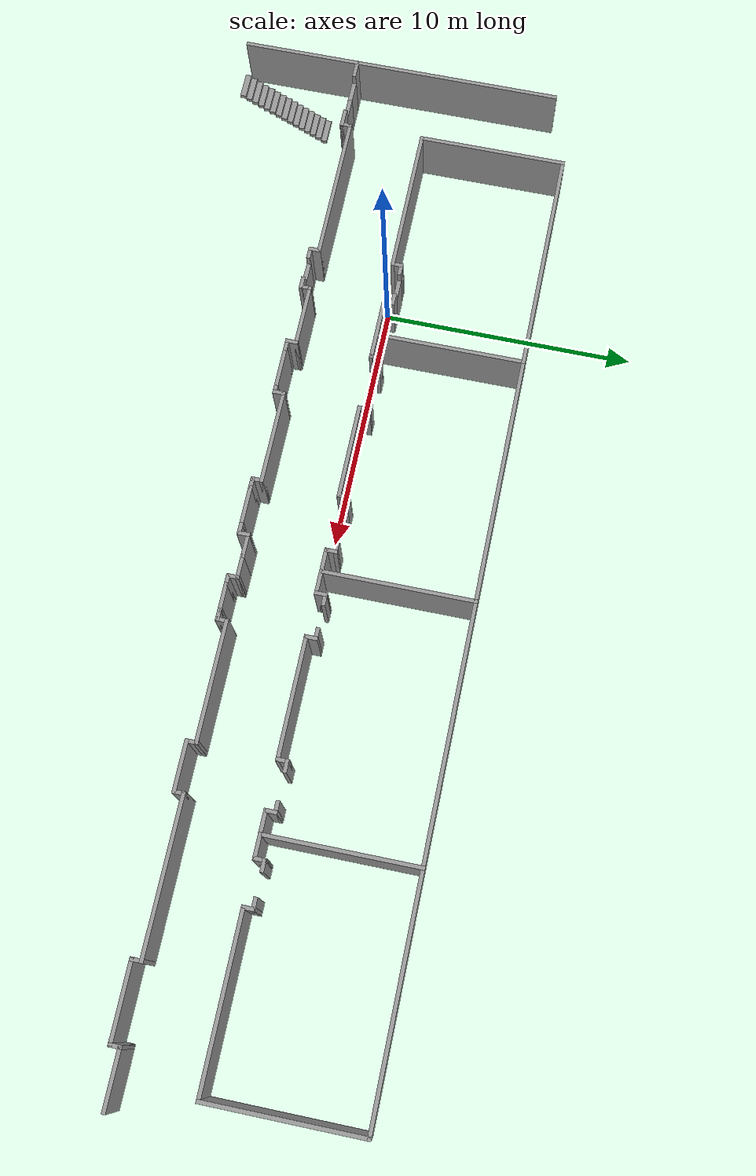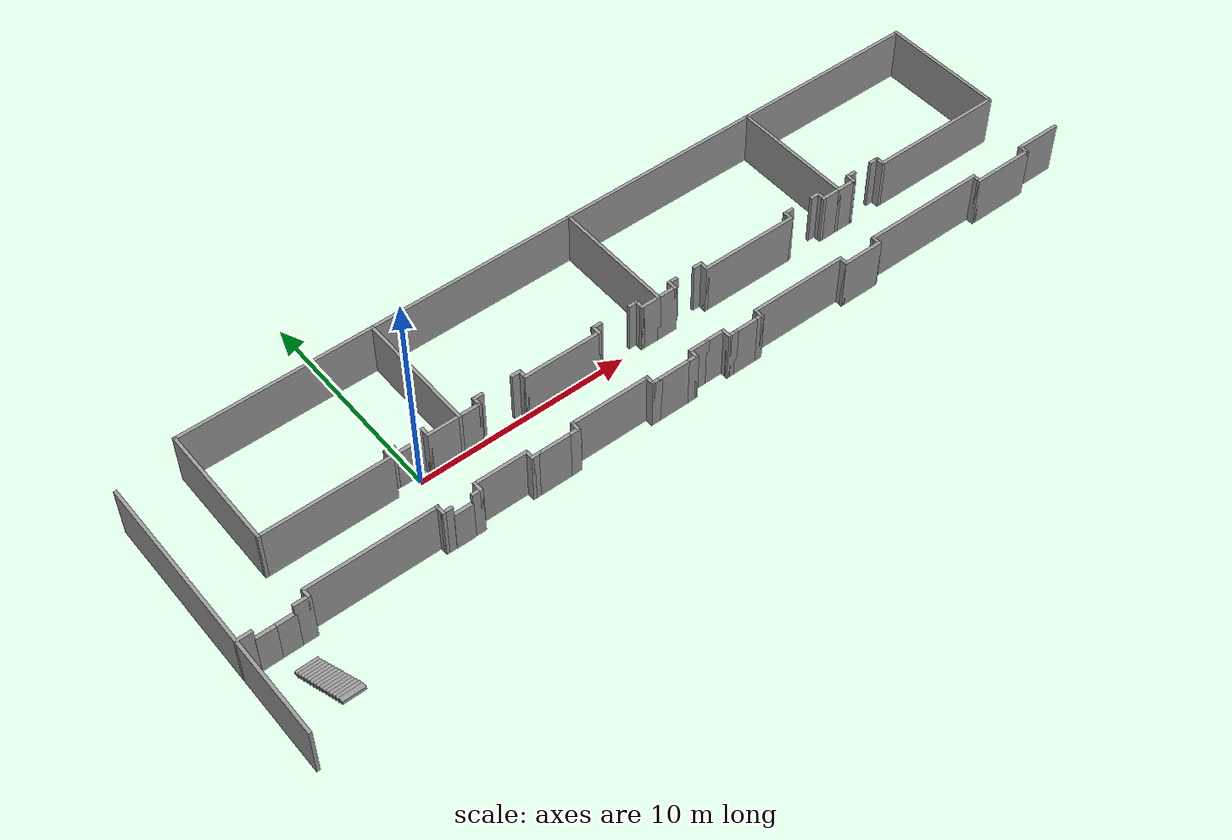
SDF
<?xml version='1.0'?>
<sdf version='1.6'>
  <model name='corridor'>
    <pose frame=''>10.825 -1.075 0 0 -0 0</pose>
    <link name='Door_1'>
      <collision name='Door_1_Collision'>
        <geometry>
          <box>
            <size>0.9 0.17 2</size>
          </box>
        </geometry>
        <pose frame=''>0 0 1 0 -0 0</pose>
      </collision>
      <visual name='Door_1_Visual'>
        <pose frame=''>0 0 1 0 -0 0</pose>
        <geometry>
          <box>
            <size>0.9 0.17 2</size>
          </box>
        </geometry>
        <material>
          <script>
            <uri>file://media/materials/scripts/gazebo.material</uri>
            <name>Gazebo/Grey</name>
          </script>
        </material>
      </visual>
      <pose frame=''>-18.8694 -2.273 0 0 -0 0</pose>
    </link>
    <link name='Door_4'>
      <collision name='Door_4_Collision'>
        <geometry>
          <box>
            <size>0.9 0.17 2</size>
          </box>
        </geometry>
        <pose frame=''>0 0 1 0 -0 0</pose>
      </collision>
      <visual name='Door_4_Visual'>
        <pose frame=''>0 0 1 0 -0 0</pose>
        <geometry>
          <box>
            <size>0.9 0.17 2</size>
          </box>
        </geometry>
        <material>
          <script>
            <uri>file://media/materials/scripts/gazebo.material</uri>
            <name>Gazebo/Grey</name>
          </script>
        </material>
      </visual>
      <pose frame=''>-11.125 1.425 0 0 -0 3.14042</pose>
    </link>
    <link name='Door_6'>
      <collision name='Door_6_Collision'>
        <geometry>
          <box>
            <size>0.9 0.17 2</size>
          </box>
        </geometry>
        <pose frame=''>0 0 1 0 -0 0</pose>
      </collision>
      <visual name='Door_6_Visual'>
        <pose frame=''>0 0 1 0 -0 0</pose>
        <geometry>
          <box>
            <size>0.9 0.17 2</size>
          </box>
        </geometry>
        <material>
          <script>
            <uri>file://media/materials/scripts/gazebo.material</uri>
            <name>Gazebo/Grey</name>
          </script>
        </material>
      </visual>
      <pose frame=''>-19.7205 -2.27816 0 0 -0 0</pose>
    </link>
    <link name='Door_7'>
      <collision name='Door_7_Collision'>
        <geometry>
          <box>
            <size>0.9 0.17 2</size>
          </box>
        </geometry>
        <pose frame=''>0 0 1 0 -0 0</pose>
      </collision>
      <visual name='Door_7_Visual'>
        <pose frame=''>0 0 1 0 -0 0</pose>
        <geometry>
          <box>
            <size>0.9 0.17 2</size>
          </box>
        </geometry>
        <material>
          <script>
            <uri>file://media/materials/scripts/gazebo.material</uri>
            <name>Gazebo/Grey</name>
          </script>
        </material>
      </visual>
      <pose frame=''>-11.125 -2.279 0 0 -0 0</pose>
    </link>
    <link name='Stairs_1'>
      <visual name='Stairs_1_Visual_0'>
        <pose frame=''>-18.825 -3.29167 0.083333 0 -0 0</pose>
        <geometry>
          <box>
            <size>1 0.233333 0.166667</size>
          </box>
        </geometry>
        <material>
          <script>
            <uri>file://media/materials/scripts/gazebo.material</uri>
            <name>Gazebo/Grey</name>
          </script>
          <ambient>1 1 1 1</ambient>
        </material>
        <meta>
          <layer>0</layer>
        </meta>
      </visual>
      <collision name='Stairs_1_Collision_0'>
        <geometry>
          <box>
            <size>1 0.233333 0.166667</size>
          </box>
        </geometry>
        <pose frame=''>-18.825 -3.29167 0.083333 0 -0 0</pose>
      </collision>
      <visual name='Stairs_1_Visual_1'>
        <pose frame=''>-18.825 -3.525 0.25 0 -0 0</pose>
        <geometry>
          <box>
            <size>1 0.233333 0.166667</size>
          </box>
        </geometry>
        <material>
          <script>
            <uri>file://media/materials/scripts/gazebo.material</uri>
            <name>Gazebo/Grey</name>
          </script>
          <ambient>1 1 1 1</ambient>
        </material>
        <meta>
          <layer>0</layer>
        </meta>
      </visual>
      <collision name='Stairs_1_Collision_1'>
        <geometry>
          <box>
            <size>1 0.233333 0.166667</size>
          </box>
        </geometry>
        <pose frame=''>-18.825 -3.525 0.25 0 -0 0</pose>
      </collision>
      <visual name='Stairs_1_Visual_2'>
        <pose frame=''>-18.825 -3.75833 0.416667 0 -0 0</pose>
        <geometry>
          <box>
            <size>1 0.233333 0.166667</size>
          </box>
        </geometry>
        <material>
          <script>
            <uri>file://media/materials/scripts/gazebo.material</uri>
            <name>Gazebo/Grey</name>
          </script>
          <ambient>1 1 1 1</ambient>
        </material>
        <meta>
          <layer>0</layer>
        </meta>
      </visual>
      <collision name='Stairs_1_Collision_2'>
        <geometry>
          <box>
            <size>1 0.233333 0.166667</size>
          </box>
        </geometry>
        <pose frame=''>-18.825 -3.75833 0.416667 0 -0 0</pose>
      </collision>
      <visual name='Stairs_1_Visual_3'>
        <pose frame=''>-18.825 -3.99167 0.583333 0 -0 0</pose>
        <geometry>
          <box>
            <size>1 0.233333 0.166667</size>
          </box>
        </geometry>
        <material>
          <script>
            <uri>file://media/materials/scripts/gazebo.material</uri>
            <name>Gazebo/Grey</name>
          </script>
          <ambient>1 1 1 1</ambient>
        </material>
        <meta>
          <layer>0</layer>
        </meta>
      </visual>
      <collision name='Stairs_1_Collision_3'>
        <geometry>
          <box>
            <size>1 0.233333 0.166667</size>
          </box>
        </geometry>
        <pose frame=''>-18.825 -3.99167 0.583333 0 -0 0</pose>
      </collision>
      <visual name='Stairs_1_Visual_4'>
        <pose frame=''>-18.825 -4.225 0.75 0 -0 0</pose>
        <geometry>
          <box>
            <size>1 0.233333 0.166667</size>
          </box>
        </geometry>
        <material>
          <script>
            <uri>file://media/materials/scripts/gazebo.material</uri>
            <name>Gazebo/Grey</name>
          </script>
          <ambient>1 1 1 1</ambient>
        </material>
        <meta>
          <layer>0</layer>
        </meta>
      </visual>
      <collision name='Stairs_1_Collision_4'>
        <geometry>
          <box>
            <size>1 0.233333 0.166667</size>
          </box>
        </geometry>
        <pose frame=''>-18.825 -4.225 0.75 0 -0 0</pose>
      </collision>
      <visual name='Stairs_1_Visual_5'>
        <pose frame=''>-18.825 -4.45833 0.916667 0 -0 0</pose>
        <geometry>
          <box>
            <size>1 0.233333 0.166667</size>
          </box>
        </geometry>
        <material>
          <script>
            <uri>file://media/materials/scripts/gazebo.material</uri>
            <name>Gazebo/Grey</name>
          </script>
          <ambient>1 1 1 1</ambient>
        </material>
        <meta>
          <layer>0</layer>
        </meta>
      </visual>
      <collision name='Stairs_1_Collision_5'>
        <geometry>
          <box>
            <size>1 0.233333 0.166667</size>
          </box>
        </geometry>
        <pose frame=''>-18.825 -4.45833 0.916667 0 -0 0</pose>
      </collision>
      <visual name='Stairs_1_Visual_6'>
        <pose frame=''>-18.825 -4.69167 1.08333 0 -0 0</pose>
        <geometry>
          <box>
            <size>1 0.233333 0.166667</size>
          </box>
        </geometry>
        <material>
          <script>
            <uri>file://media/materials/scripts/gazebo.material</uri>
            <name>Gazebo/Grey</name>
          </script>
          <ambient>1 1 1 1</ambient>
        </material>
        <meta>
          <layer>0</layer>
        </meta>
      </visual>
      <collision name='Stairs_1_Collision_6'>
        <geometry>
          <box>
            <size>1 0.233333 0.166667</size>
          </box>
        </geometry>
        <pose frame=''>-18.825 -4.69167 1.08333 0 -0 0</pose>
      </collision>
      <visual name='Stairs_1_Visual_7'>
        <pose frame=''>-18.825 -4.925 1.25 0 -0 0</pose>
        <geometry>
          <box>
            <size>1 0.233333 0.166667</size>
          </box>
        </geometry>
        <material>
          <script>
            <uri>file://media/materials/scripts/gazebo.material</uri>
            <name>Gazebo/Grey</name>
          </script>
          <ambient>1 1 1 1</ambient>
        </material>
        <meta>
          <layer>0</layer>
        </meta>
      </visual>
      <collision name='Stairs_1_Collision_7'>
        <geometry>
          <box>
            <size>1 0.233333 0.166667</size>
          </box>
        </geometry>
        <pose frame=''>-18.825 -4.925 1.25 0 -0 0</pose>
      </collision>
      <visual name='Stairs_1_Visual_8'>
        <pose frame=''>-18.825 -5.15833 1.41667 0 -0 0</pose>
        <geometry>
          <box>
            <size>1 0.233333 0.166667</size>
          </box>
        </geometry>
        <material>
          <script>
            <uri>file://media/materials/scripts/gazebo.material</uri>
            <name>Gazebo/Grey</name>
          </script>
          <ambient>1 1 1 1</ambient>
        </material>
        <meta>
          <layer>0</layer>
        </meta>
      </visual>
      <collision name='Stairs_1_Collision_8'>
        <geometry>
          <box>
            <size>1 0.233333 0.166667</size>
          </box>
        </geometry>
        <pose frame=''>-18.825 -5.15833 1.41667 0 -0 0</pose>
      </collision>
      <visual name='Stairs_1_Visual_9'>
        <pose frame=''>-18.825 -5.39167 1.58333 0 -0 0</pose>
        <geometry>
          <box>
            <size>1 0.233333 0.166667</size>
          </box>
        </geometry>
        <material>
          <script>
            <uri>file://media/materials/scripts/gazebo.material</uri>
            <name>Gazebo/Grey</name>
          </script>
          <ambient>1 1 1 1</ambient>
        </material>
        <meta>
          <layer>0</layer>
        </meta>
      </visual>
      <collision name='Stairs_1_Collision_9'>
        <geometry>
          <box>
            <size>1 0.233333 0.166667</size>
          </box>
        </geometry>
        <pose frame=''>-18.825 -5.39167 1.58333 0 -0 0</pose>
      </collision>
      <visual name='Stairs_1_Visual_10'>
        <pose frame=''>-18.825 -5.625 1.75 0 -0 0</pose>
        <geometry>
          <box>
            <size>1 0.233333 0.166667</size>
          </box>
        </geometry>
        <material>
          <script>
            <uri>file://media/materials/scripts/gazebo.material</uri>
            <name>Gazebo/Grey</name>
          </script>
          <ambient>1 1 1 1</ambient>
        </material>
        <meta>
          <layer>0</layer>
        </meta>
      </visual>
      <collision name='Stairs_1_Collision_10'>
        <geometry>
          <box>
            <size>1 0.233333 0.166667</size>
          </box>
        </geometry>
        <pose frame=''>-18.825 -5.625 1.75 0 -0 0</pose>
      </collision>
      <visual name='Stairs_1_Visual_11'>
        <pose frame=''>-18.825 -5.85833 1.91667 0 -0 0</pose>
        <geometry>
          <box>
            <size>1 0.233333 0.166667</size>
          </box>
        </geometry>
        <material>
          <script>
            <uri>file://media/materials/scripts/gazebo.material</uri>
            <name>Gazebo/Grey</name>
          </script>
          <ambient>1 1 1 1</ambient>
        </material>
        <meta>
          <layer>0</layer>
        </meta>
      </visual>
      <collision name='Stairs_1_Collision_11'>
        <geometry>
          <box>
            <size>1 0.233333 0.166667</size>
          </box>
        </geometry>
        <pose frame=''>-18.825 -5.85833 1.91667 0 -0 0</pose>
      </collision>
      <visual name='Stairs_1_Visual_12'>
        <pose frame=''>-18.825 -6.09167 2.08333 0 -0 0</pose>
        <geometry>
          <box>
            <size>1 0.233333 0.166667</size>
          </box>
        </geometry>
        <material>
          <script>
            <uri>file://media/materials/scripts/gazebo.material</uri>
            <name>Gazebo/Grey</name>
          </script>
          <ambient>1 1 1 1</ambient>
        </material>
        <meta>
          <layer>0</layer>
        </meta>
      </visual>
      <collision name='Stairs_1_Collision_12'>
        <geometry>
          <box>
            <size>1 0.233333 0.166667</size>
          </box>
        </geometry>
        <pose frame=''>-18.825 -6.09167 2.08333 0 -0 0</pose>
      </collision>
      <visual name='Stairs_1_Visual_13'>
        <pose frame=''>-18.825 -6.325 2.25 0 -0 0</pose>
        <geometry>
          <box>
            <size>1 0.233333 0.166667</size>
          </box>
        </geometry>
        <material>
          <script>
            <uri>file://media/materials/scripts/gazebo.material</uri>
            <name>Gazebo/Grey</name>
          </script>
          <ambient>1 1 1 1</ambient>
        </material>
        <meta>
          <layer>0</layer>
        </meta>
      </visual>
      <collision name='Stairs_1_Collision_13'>
        <geometry>
          <box>
            <size>1 0.233333 0.166667</size>
          </box>
        </geometry>
        <pose frame=''>-18.825 -6.325 2.25 0 -0 0</pose>
      </collision>
      <visual name='Stairs_1_Visual_14'>
        <pose frame=''>-18.825 -6.55833 2.41667 0 -0 0</pose>
        <geometry>
          <box>
            <size>1 0.233333 0.166667</size>
          </box>
        </geometry>
        <material>
          <script>
            <uri>file://media/materials/scripts/gazebo.material</uri>
            <name>Gazebo/Grey</name>
          </script>
          <ambient>1 1 1 1</ambient>
        </material>
        <meta>
          <layer>0</layer>
        </meta>
      </visual>
      <collision name='Stairs_1_Collision_14'>
        <geometry>
          <box>
            <size>1 0.233333 0.166667</size>
          </box>
        </geometry>
        <pose frame=''>-18.825 -6.55833 2.41667 0 -0 0</pose>
      </collision>
    </link>
    <link name='Wall_0'>
      <collision name='Wall_0_Collision'>
        <geometry>
          <box>
            <size>6 0.15 2.5</size>
          </box>
        </geometry>
        <pose frame=''>0 0 1.25 0 -0 0</pose>
      </collision>
      <visual name='Wall_0_Visual'>
        <pose frame=''>0 0 1.25 0 -0 0</pose>
        <geometry>
          <box>
            <size>6 0.15 2.5</size>
          </box>
        </geometry>
        <material>
          <script>
            <uri>file://media/materials/scripts/gazebo.material</uri>
            <name>Gazebo/Grey</name>
          </script>
          <ambient>1 1 1 1</ambient>
        </material>
        <meta>
          <layer>0</layer>
        </meta>
      </visual>
      <pose frame=''>-14.9 1.075 0 0 -0 3.14159</pose>
    </link>
    <link name='Wall_100'>
      <collision name='Wall_100_Collision'>
        <geometry>
          <box>
            <size>0.5 0.15 2.5</size>
          </box>
        </geometry>
        <pose frame=''>0 0 1.25 0 -0 0</pose>
      </collision>
      <visual name='Wall_100_Visual'>
        <pose frame=''>0 0 1.25 0 -0 0</pose>
        <geometry>
          <box>
            <size>0.5 0.15 2.5</size>
          </box>
        </geometry>
        <material>
          <script>
            <uri>file://media/materials/scripts/gazebo.material</uri>
            <name>Gazebo/Grey</name>
          </script>
          <ambient>1 1 1 1</ambient>
        </material>
        <meta>
          <layer>0</layer>
        </meta>
      </visual>
      <pose frame=''>-1.85 -2.275 0 0 -0 0</pose>
    </link>
    <link name='Wall_102'>
      <collision name='Wall_102_Collision'>
        <geometry>
          <box>
            <size>0.5 0.15 2.5</size>
          </box>
        </geometry>
        <pose frame=''>0 0 1.25 0 -0 0</pose>
      </collision>
      <visual name='Wall_102_Visual'>
        <pose frame=''>0 0 1.25 0 -0 0</pose>
        <geometry>
          <box>
            <size>0.5 0.15 2.5</size>
          </box>
        </geometry>
        <material>
          <script>
            <uri>file://media/materials/scripts/gazebo.material</uri>
            <name>Gazebo/Grey</name>
          </script>
          <ambient>1 1 1 1</ambient>
        </material>
        <meta>
          <layer>0</layer>
        </meta>
      </visual>
      <pose frame=''>0 -2.275 0 0 -0 3.14159</pose>
    </link>
    <link name='Wall_104'>
      <collision name='Wall_104_Collision'>
        <geometry>
          <box>
            <size>0.5 0.15 2.5</size>
          </box>
        </geometry>
        <pose frame=''>0 0 1.25 0 -0 0</pose>
      </collision>
      <visual name='Wall_104_Visual'>
        <pose frame=''>0 0 1.25 0 -0 0</pose>
        <geometry>
          <box>
            <size>0.5 0.15 2.5</size>
          </box>
        </geometry>
        <material>
          <script>
            <uri>file://media/materials/scripts/gazebo.material</uri>
            <name>Gazebo/Grey</name>
          </script>
          <ambient>1 1 1 1</ambient>
        </material>
        <meta>
          <layer>0</layer>
        </meta>
      </visual>
      <pose frame=''>0.175 -2.1 0 0 -0 1.5708</pose>
    </link>
    <link name='Wall_105'>
      <collision name='Wall_105_Collision'>
        <geometry>
          <box>
            <size>1 0.15 2.5</size>
          </box>
        </geometry>
        <pose frame=''>0 0 1.25 0 -0 0</pose>
      </collision>
      <visual name='Wall_105_Visual'>
        <pose frame=''>0 0 1.25 0 -0 0</pose>
        <geometry>
          <box>
            <size>1 0.15 2.5</size>
          </box>
        </geometry>
        <material>
          <script>
            <uri>file://media/materials/scripts/gazebo.material</uri>
            <name>Gazebo/Grey</name>
          </script>
          <ambient>1 1 1 1</ambient>
        </material>
        <meta>
          <layer>0</layer>
        </meta>
      </visual>
      <pose frame=''>0.6 -1.925 0 0 -0 0</pose>
    </link>
    <link name='Wall_11'>
      <collision name='Wall_11_Collision'>
        <geometry>
          <box>
            <size>0.75 0.15 2.5</size>
          </box>
        </geometry>
        <pose frame=''>0 0 1.25 0 -0 0</pose>
      </collision>
      <visual name='Wall_11_Visual'>
        <pose frame=''>0 0 1.25 0 -0 0</pose>
        <geometry>
          <box>
            <size>0.75 0.15 2.5</size>
          </box>
        </geometry>
        <material>
          <script>
            <uri>file://media/materials/scripts/gazebo.material</uri>
            <name>Gazebo/Grey</name>
          </script>
          <ambient>1 1 1 1</ambient>
        </material>
        <meta>
          <layer>0</layer>
        </meta>
      </visual>
      <pose frame=''>-18.125 -2.275 0 0 -0 3.14159</pose>
    </link>
    <link name='Wall_113'>
      <collision name='Wall_113_Collision'>
        <geometry>
          <box>
            <size>10 0.15 2.5</size>
          </box>
        </geometry>
        <pose frame=''>0 0 1.25 0 -0 0</pose>
      </collision>
      <visual name='Wall_113_Visual'>
        <pose frame=''>0 0 1.25 0 -0 0</pose>
        <geometry>
          <box>
            <size>10 0.15 2.5</size>
          </box>
        </geometry>
        <material>
          <script>
            <uri>file://media/materials/scripts/gazebo.material</uri>
            <name>Gazebo/Grey</name>
          </script>
          <ambient>1 1 1 1</ambient>
        </material>
        <meta>
          <layer>0</layer>
        </meta>
      </visual>
      <pose frame=''>5.95 6.925 0 0 -0 0</pose>
    </link>
    <link name='Wall_115'>
      <collision name='Wall_115_Collision'>
        <geometry>
          <box>
            <size>6 0.15 2.5</size>
          </box>
        </geometry>
        <pose frame=''>0 0 1.25 0 -0 0</pose>
      </collision>
      <visual name='Wall_115_Visual'>
        <pose frame=''>0 0 1.25 0 -0 0</pose>
        <geometry>
          <box>
            <size>6 0.15 2.5</size>
          </box>
        </geometry>
        <material>
          <script>
            <uri>file://media/materials/scripts/gazebo.material</uri>
            <name>Gazebo/Grey</name>
          </script>
          <ambient>1 1 1 1</ambient>
        </material>
        <meta>
          <layer>0</layer>
        </meta>
      </visual>
      <pose frame=''>10.875 4 0 0 0 -1.5708</pose>
    </link>
    <link name='Wall_117'>
      <collision name='Wall_117_Collision'>
        <geometry>
          <box>
            <size>1 0.15 2.5</size>
          </box>
        </geometry>
        <pose frame=''>0 0 1.25 0 -0 0</pose>
      </collision>
      <visual name='Wall_117_Visual'>
        <pose frame=''>0 0 1.25 0 -0 0</pose>
        <geometry>
          <box>
            <size>1 0.15 2.5</size>
          </box>
        </geometry>
        <material>
          <script>
            <uri>file://media/materials/scripts/gazebo.material</uri>
            <name>Gazebo/Grey</name>
          </script>
          <ambient>1 1 1 1</ambient>
        </material>
        <meta>
          <layer>0</layer>
        </meta>
      </visual>
      <pose frame=''>1.45 1.075 0 0 -0 0</pose>
    </link>
    <link name='Wall_119'>
      <collision name='Wall_119_Collision'>
        <geometry>
          <box>
            <size>0.5 0.15 2.5</size>
          </box>
        </geometry>
        <pose frame=''>0 0 1.25 0 -0 0</pose>
      </collision>
      <visual name='Wall_119_Visual'>
        <pose frame=''>0 0 1.25 0 -0 0</pose>
        <geometry>
          <box>
            <size>0.5 0.15 2.5</size>
          </box>
        </geometry>
        <material>
          <script>
            <uri>file://media/materials/scripts/gazebo.material</uri>
            <name>Gazebo/Grey</name>
          </script>
          <ambient>1 1 1 1</ambient>
        </material>
        <meta>
          <layer>0</layer>
        </meta>
      </visual>
      <pose frame=''>1.875 1.25 0 0 -0 1.5708</pose>
    </link>
    <link name='Wall_120'>
      <collision name='Wall_120_Collision'>
        <geometry>
          <box>
            <size>0.5 0.15 2.5</size>
          </box>
        </geometry>
        <pose frame=''>0 0 1.25 0 -0 0</pose>
      </collision>
      <visual name='Wall_120_Visual'>
        <pose frame=''>0 0 1.25 0 -0 0</pose>
        <geometry>
          <box>
            <size>0.5 0.15 2.5</size>
          </box>
        </geometry>
        <material>
          <script>
            <uri>file://media/materials/scripts/gazebo.material</uri>
            <name>Gazebo/Grey</name>
          </script>
          <ambient>1 1 1 1</ambient>
        </material>
        <meta>
          <layer>0</layer>
        </meta>
      </visual>
      <pose frame=''>2.05 1.425 0 0 -0 0</pose>
    </link>
    <link name='Wall_122'>
      <collision name='Wall_122_Collision'>
        <geometry>
          <box>
            <size>0.5 0.15 2.5</size>
          </box>
        </geometry>
        <pose frame=''>0 0 1.25 0 -0 0</pose>
      </collision>
      <visual name='Wall_122_Visual'>
        <pose frame=''>0 0 1.25 0 -0 0</pose>
        <geometry>
          <box>
            <size>0.5 0.15 2.5</size>
          </box>
        </geometry>
        <material>
          <script>
            <uri>file://media/materials/scripts/gazebo.material</uri>
            <name>Gazebo/Grey</name>
          </script>
          <ambient>1 1 1 1</ambient>
        </material>
        <meta>
          <layer>0</layer>
        </meta>
      </visual>
      <pose frame=''>3.4 1.433 0 0 -0 0</pose>
    </link>
    <link name='Wall_124'>
      <collision name='Wall_124_Collision'>
        <geometry>
          <box>
            <size>0.508 0.15 2.5</size>
          </box>
        </geometry>
        <pose frame=''>0 0 1.25 0 -0 0</pose>
      </collision>
      <visual name='Wall_124_Visual'>
        <pose frame=''>0 0 1.25 0 -0 0</pose>
        <geometry>
          <box>
            <size>0.508 0.15 2.5</size>
          </box>
        </geometry>
        <material>
          <script>
            <uri>file://media/materials/scripts/gazebo.material</uri>
            <name>Gazebo/Grey</name>
          </script>
          <ambient>1 1 1 1</ambient>
        </material>
        <meta>
          <layer>0</layer>
        </meta>
      </visual>
      <pose frame=''>3.575 1.254 0 0 0 -1.5708</pose>
    </link>
    <link name='Wall_125'>
      <collision name='Wall_125_Collision'>
        <geometry>
          <box>
            <size>4.75 0.15 2.5</size>
          </box>
        </geometry>
        <pose frame=''>0 0 1.25 0 -0 0</pose>
      </collision>
      <visual name='Wall_125_Visual'>
        <pose frame=''>0 0 1.25 0 -0 0</pose>
        <geometry>
          <box>
            <size>4.75 0.15 2.5</size>
          </box>
        </geometry>
        <material>
          <script>
            <uri>file://media/materials/scripts/gazebo.material</uri>
            <name>Gazebo/Grey</name>
          </script>
          <ambient>1 1 1 1</ambient>
        </material>
        <meta>
          <layer>0</layer>
        </meta>
      </visual>
      <pose frame=''>5.875 1.075 0 0 -0 0</pose>
    </link>
    <link name='Wall_127'>
      <collision name='Wall_127_Collision'>
        <geometry>
          <box>
            <size>1 0.15 2.5</size>
          </box>
        </geometry>
        <pose frame=''>0 0 1.25 0 -0 0</pose>
      </collision>
      <visual name='Wall_127_Visual'>
        <pose frame=''>0 0 1.25 0 -0 0</pose>
        <geometry>
          <box>
            <size>1 0.15 2.5</size>
          </box>
        </geometry>
        <material>
          <script>
            <uri>file://media/materials/scripts/gazebo.material</uri>
            <name>Gazebo/Grey</name>
          </script>
          <ambient>1 1 1 1</ambient>
        </material>
        <meta>
          <layer>0</layer>
        </meta>
      </visual>
      <pose frame=''>10.45 1.075 0 0 -0 3.14159</pose>
    </link>
    <link name='Wall_13'>
      <collision name='Wall_13_Collision'>
        <geometry>
          <box>
            <size>0.75 0.15 2.5</size>
          </box>
        </geometry>
        <pose frame=''>0 0 1.25 0 -0 0</pose>
      </collision>
      <visual name='Wall_13_Visual'>
        <pose frame=''>0 0 1.25 0 -0 0</pose>
        <geometry>
          <box>
            <size>0.75 0.15 2.5</size>
          </box>
        </geometry>
        <material>
          <script>
            <uri>file://media/materials/scripts/gazebo.material</uri>
            <name>Gazebo/Grey</name>
          </script>
          <ambient>1 1 1 1</ambient>
        </material>
        <meta>
          <layer>0</layer>
        </meta>
      </visual>
      <pose frame=''>-20.525 -2.275 0 0 -0 0</pose>
    </link>
    <link name='Wall_131'>
      <collision name='Wall_131_Collision'>
        <geometry>
          <box>
            <size>0.5 0.15 2.5</size>
          </box>
        </geometry>
        <pose frame=''>0 0 1.25 0 -0 0</pose>
      </collision>
      <visual name='Wall_131_Visual'>
        <pose frame=''>0 0 1.25 0 -0 0</pose>
        <geometry>
          <box>
            <size>0.5 0.15 2.5</size>
          </box>
        </geometry>
        <material>
          <script>
            <uri>file://media/materials/scripts/gazebo.material</uri>
            <name>Gazebo/Grey</name>
          </script>
          <ambient>1 1 1 1</ambient>
        </material>
        <meta>
          <layer>0</layer>
        </meta>
      </visual>
      <pose frame=''>10.025 1.25 0 0 -0 1.5708</pose>
    </link>
    <link name='Wall_132'>
      <collision name='Wall_132_Collision'>
        <geometry>
          <box>
            <size>0.5 0.15 2.5</size>
          </box>
        </geometry>
        <pose frame=''>0 0 1.25 0 -0 0</pose>
      </collision>
      <visual name='Wall_132_Visual'>
        <pose frame=''>0 0 1.25 0 -0 0</pose>
        <geometry>
          <box>
            <size>0.5 0.15 2.5</size>
          </box>
        </geometry>
        <material>
          <script>
            <uri>file://media/materials/scripts/gazebo.material</uri>
            <name>Gazebo/Grey</name>
          </script>
          <ambient>1 1 1 1</ambient>
        </material>
        <meta>
          <layer>0</layer>
        </meta>
      </visual>
      <pose frame=''>9.85 1.425 0 0 -0 3.14159</pose>
    </link>
    <link name='Wall_134'>
      <collision name='Wall_134_Collision'>
        <geometry>
          <box>
            <size>0.5 0.15 2.5</size>
          </box>
        </geometry>
        <pose frame=''>0 0 1.25 0 -0 0</pose>
      </collision>
      <visual name='Wall_134_Visual'>
        <pose frame=''>0 0 1.25 0 -0 0</pose>
        <geometry>
          <box>
            <size>0.5 0.15 2.5</size>
          </box>
        </geometry>
        <material>
          <script>
            <uri>file://media/materials/scripts/gazebo.material</uri>
            <name>Gazebo/Grey</name>
          </script>
          <ambient>1 1 1 1</ambient>
        </material>
        <meta>
          <layer>0</layer>
        </meta>
      </visual>
      <pose frame=''>8.35 1.425 0 0 -0 3.14159</pose>
    </link>
    <link name='Wall_138'>
      <collision name='Wall_138_Collision'>
        <geometry>
          <box>
            <size>1 0.15 2.5</size>
          </box>
        </geometry>
        <pose frame=''>0 0 1.25 0 -0 0</pose>
      </collision>
      <visual name='Wall_138_Visual'>
        <pose frame=''>0 0 1.25 0 -0 0</pose>
        <geometry>
          <box>
            <size>1 0.15 2.5</size>
          </box>
        </geometry>
        <material>
          <script>
            <uri>file://media/materials/scripts/gazebo.material</uri>
            <name>Gazebo/Grey</name>
          </script>
          <ambient>1 1 1 1</ambient>
        </material>
        <meta>
          <layer>0</layer>
        </meta>
      </visual>
      <pose frame=''>1.45 -1.925 0 0 -0 0</pose>
    </link>
    <link name='Wall_139'>
      <collision name='Wall_139_Collision'>
        <geometry>
          <box>
            <size>0.5 0.15 2.5</size>
          </box>
        </geometry>
        <pose frame=''>0 0 1.25 0 -0 0</pose>
      </collision>
      <visual name='Wall_139_Visual'>
        <pose frame=''>0 0 1.25 0 -0 0</pose>
        <geometry>
          <box>
            <size>0.5 0.15 2.5</size>
          </box>
        </geometry>
        <material>
          <script>
            <uri>file://media/materials/scripts/gazebo.material</uri>
            <name>Gazebo/Grey</name>
          </script>
          <ambient>1 1 1 1</ambient>
        </material>
        <meta>
          <layer>0</layer>
        </meta>
      </visual>
      <pose frame=''>1.875 -2.1 0 0 0 -1.5708</pose>
    </link>
    <link name='Wall_140'>
      <collision name='Wall_140_Collision'>
        <geometry>
          <box>
            <size>0.5 0.15 2.5</size>
          </box>
        </geometry>
        <pose frame=''>0 0 1.25 0 -0 0</pose>
      </collision>
      <visual name='Wall_140_Visual'>
        <pose frame=''>0 0 1.25 0 -0 0</pose>
        <geometry>
          <box>
            <size>0.5 0.15 2.5</size>
          </box>
        </geometry>
        <material>
          <script>
            <uri>file://media/materials/scripts/gazebo.material</uri>
            <name>Gazebo/Grey</name>
          </script>
          <ambient>1 1 1 1</ambient>
        </material>
        <meta>
          <layer>0</layer>
        </meta>
      </visual>
      <pose frame=''>2.05 -2.275 0 0 -0 0</pose>
    </link>
    <link name='Wall_142'>
      <collision name='Wall_142_Collision'>
        <geometry>
          <box>
            <size>0.5 0.15 2.5</size>
          </box>
        </geometry>
        <pose frame=''>0 0 1.25 0 -0 0</pose>
      </collision>
      <visual name='Wall_142_Visual'>
        <pose frame=''>0 0 1.25 0 -0 0</pose>
        <geometry>
          <box>
            <size>0.5 0.15 2.5</size>
          </box>
        </geometry>
        <material>
          <script>
            <uri>file://media/materials/scripts/gazebo.material</uri>
            <name>Gazebo/Grey</name>
          </script>
          <ambient>1 1 1 1</ambient>
        </material>
        <meta>
          <layer>0</layer>
        </meta>
      </visual>
      <pose frame=''>8.175 1.25 0 0 0 -1.5708</pose>
    </link>
    <link name='Wall_147'>
      <collision name='Wall_147_Collision'>
        <geometry>
          <box>
            <size>4.75 0.15 2.5</size>
          </box>
        </geometry>
        <pose frame=''>0 0 1.25 0 -0 0</pose>
      </collision>
      <visual name='Wall_147_Visual'>
        <pose frame=''>0 0 1.25 0 -0 0</pose>
        <geometry>
          <box>
            <size>4.75 0.15 2.5</size>
          </box>
        </geometry>
        <material>
          <script>
            <uri>file://media/materials/scripts/gazebo.material</uri>
            <name>Gazebo/Grey</name>
          </script>
          <ambient>1 1 1 1</ambient>
        </material>
        <meta>
          <layer>0</layer>
        </meta>
      </visual>
      <pose frame=''>5.875 -1.925 0 0 -0 0</pose>
    </link>
    <link name='Wall_150'>
      <collision name='Wall_150_Collision'>
        <geometry>
          <box>
            <size>0.5 0.15 2.5</size>
          </box>
        </geometry>
        <pose frame=''>0 0 1.25 0 -0 0</pose>
      </collision>
      <visual name='Wall_150_Visual'>
        <pose frame=''>0 0 1.25 0 -0 0</pose>
        <geometry>
          <box>
            <size>0.5 0.15 2.5</size>
          </box>
        </geometry>
        <material>
          <script>
            <uri>file://media/materials/scripts/gazebo.material</uri>
            <name>Gazebo/Grey</name>
          </script>
          <ambient>1 1 1 1</ambient>
        </material>
        <meta>
          <layer>0</layer>
        </meta>
      </visual>
      <pose frame=''>3.575 -2.1 0 0 0 -1.5708</pose>
    </link>
    <link name='Wall_151'>
      <collision name='Wall_151_Collision'>
        <geometry>
          <box>
            <size>0.5 0.15 2.5</size>
          </box>
        </geometry>
        <pose frame=''>0 0 1.25 0 -0 0</pose>
      </collision>
      <visual name='Wall_151_Visual'>
        <pose frame=''>0 0 1.25 0 -0 0</pose>
        <geometry>
          <box>
            <size>0.5 0.15 2.5</size>
          </box>
        </geometry>
        <material>
          <script>
            <uri>file://media/materials/scripts/gazebo.material</uri>
            <name>Gazebo/Grey</name>
          </script>
          <ambient>1 1 1 1</ambient>
        </material>
        <meta>
          <layer>0</layer>
        </meta>
      </visual>
      <pose frame=''>3.4 -2.275 0 0 -0 3.14159</pose>
    </link>
    <link name='Wall_155'>
      <collision name='Wall_155_Collision'>
        <geometry>
          <box>
            <size>1.65 0.15 2.5</size>
          </box>
        </geometry>
        <pose frame=''>0 0 1.25 0 -0 0</pose>
      </collision>
      <visual name='Wall_155_Visual'>
        <pose frame=''>0 0 1.25 0 -0 0</pose>
        <geometry>
          <box>
            <size>1.65 0.15 2.5</size>
          </box>
        </geometry>
        <material>
          <script>
            <uri>file://media/materials/scripts/gazebo.material</uri>
            <name>Gazebo/Grey</name>
          </script>
          <ambient>1 1 1 1</ambient>
        </material>
        <meta>
          <layer>0</layer>
        </meta>
      </visual>
      <pose frame=''>-6.775 -2.275 0 0 -0 0</pose>
    </link>
    <link name='Wall_157'>
      <collision name='Wall_157_Collision'>
        <geometry>
          <box>
            <size>1.65 0.15 2.5</size>
          </box>
        </geometry>
        <pose frame=''>0 0 1.25 0 -0 0</pose>
      </collision>
      <visual name='Wall_157_Visual'>
        <pose frame=''>0 0 1.25 0 -0 0</pose>
        <geometry>
          <box>
            <size>1.65 0.15 2.5</size>
          </box>
        </geometry>
        <material>
          <script>
            <uri>file://media/materials/scripts/gazebo.material</uri>
            <name>Gazebo/Grey</name>
          </script>
          <ambient>1 1 1 1</ambient>
        </material>
        <meta>
          <layer>0</layer>
        </meta>
      </visual>
      <pose frame=''>-0.925 -2.275 0 0 -0 0</pose>
    </link>
    <link name='Wall_159'>
      <collision name='Wall_159_Collision'>
        <geometry>
          <box>
            <size>1.15 0.15 2.5</size>
          </box>
        </geometry>
        <pose frame=''>0 0 1.25 0 -0 0</pose>
      </collision>
      <visual name='Wall_159_Visual'>
        <pose frame=''>0 0 1.25 0 -0 0</pose>
        <geometry>
          <box>
            <size>1.15 0.15 2.5</size>
          </box>
        </geometry>
        <material>
          <script>
            <uri>file://media/materials/scripts/gazebo.material</uri>
            <name>Gazebo/Grey</name>
          </script>
          <ambient>1 1 1 1</ambient>
        </material>
        <meta>
          <layer>0</layer>
        </meta>
      </visual>
      <pose frame=''>2.725 -2.275 0 0 -0 0</pose>
    </link>
    <link name='Wall_16'>
      <collision name='Wall_16_Collision'>
        <geometry>
          <box>
            <size>0.5 0.15 2.5</size>
          </box>
        </geometry>
        <pose frame=''>0 0 1.25 0 -0 0</pose>
      </collision>
      <visual name='Wall_16_Visual'>
        <pose frame=''>0 0 1.25 0 -0 0</pose>
        <geometry>
          <box>
            <size>0.5 0.15 2.5</size>
          </box>
        </geometry>
        <material>
          <script>
            <uri>file://media/materials/scripts/gazebo.material</uri>
            <name>Gazebo/Grey</name>
          </script>
          <ambient>1 1 1 1</ambient>
        </material>
        <meta>
          <layer>0</layer>
        </meta>
      </visual>
      <pose frame=''>-11.975 1.25 0 0 -0 1.5708</pose>
    </link>
    <link name='Wall_161'>
      <collision name='Wall_161_Collision'>
        <geometry>
          <box>
            <size>0.5 0.15 2.5</size>
          </box>
        </geometry>
        <pose frame=''>0 0 1.25 0 -0 0</pose>
      </collision>
      <visual name='Wall_161_Visual'>
        <pose frame=''>0 0 1.25 0 -0 0</pose>
        <geometry>
          <box>
            <size>0.5 0.15 2.5</size>
          </box>
        </geometry>
        <material>
          <script>
            <uri>file://media/materials/scripts/gazebo.material</uri>
            <name>Gazebo/Grey</name>
          </script>
          <ambient>1 1 1 1</ambient>
        </material>
        <meta>
          <layer>0</layer>
        </meta>
      </visual>
      <pose frame=''>8.175 -2.1 0 0 0 -1.5708</pose>
    </link>
    <link name='Wall_162'>
      <collision name='Wall_162_Collision'>
        <geometry>
          <box>
            <size>2 0.15 2.5</size>
          </box>
        </geometry>
        <pose frame=''>0 0 1.25 0 -0 0</pose>
      </collision>
      <visual name='Wall_162_Visual'>
        <pose frame=''>0 0 1.25 0 -0 0</pose>
        <geometry>
          <box>
            <size>2 0.15 2.5</size>
          </box>
        </geometry>
        <material>
          <script>
            <uri>file://media/materials/scripts/gazebo.material</uri>
            <name>Gazebo/Grey</name>
          </script>
          <ambient>1 1 1 1</ambient>
        </material>
        <meta>
          <layer>0</layer>
        </meta>
      </visual>
      <pose frame=''>9.1 -2.275 0 0 -0 0</pose>
    </link>
    <link name='Wall_164'>
      <collision name='Wall_164_Collision'>
        <geometry>
          <box>
            <size>0.5 0.15 2.5</size>
          </box>
        </geometry>
        <pose frame=''>0 0 1.25 0 -0 0</pose>
      </collision>
      <visual name='Wall_164_Visual'>
        <pose frame=''>0 0 1.25 0 -0 0</pose>
        <geometry>
          <box>
            <size>0.5 0.15 2.5</size>
          </box>
        </geometry>
        <material>
          <script>
            <uri>file://media/materials/scripts/gazebo.material</uri>
            <name>Gazebo/Grey</name>
          </script>
          <ambient>1 1 1 1</ambient>
        </material>
        <meta>
          <layer>0</layer>
        </meta>
      </visual>
      <pose frame=''>10.025 -2.1 0 0 -0 1.5708</pose>
    </link>
    <link name='Wall_165'>
      <collision name='Wall_165_Collision'>
        <geometry>
          <box>
            <size>6 0.15 2.5</size>
          </box>
        </geometry>
        <pose frame=''>0 0 1.25 0 -0 0</pose>
      </collision>
      <visual name='Wall_165_Visual'>
        <pose frame=''>0 0 1.25 0 -0 0</pose>
        <geometry>
          <box>
            <size>6 0.15 2.5</size>
          </box>
        </geometry>
        <material>
          <script>
            <uri>file://media/materials/scripts/gazebo.material</uri>
            <name>Gazebo/Grey</name>
          </script>
          <ambient>1 1 1 1</ambient>
        </material>
        <meta>
          <layer>0</layer>
        </meta>
      </visual>
      <pose frame=''>12.95 -1.925 0 0 -0 0</pose>
    </link>
    <link name='Wall_167'>
      <collision name='Wall_167_Collision'>
        <geometry>
          <box>
            <size>9.15 0.15 2.5</size>
          </box>
        </geometry>
        <pose frame=''>0 0 1.25 0 -0 0</pose>
      </collision>
      <visual name='Wall_167_Visual'>
        <pose frame=''>0 0 1.25 0 -0 0</pose>
        <geometry>
          <box>
            <size>9.15 0.15 2.5</size>
          </box>
        </geometry>
        <material>
          <script>
            <uri>file://media/materials/scripts/gazebo.material</uri>
            <name>Gazebo/Grey</name>
          </script>
          <ambient>1 1 1 1</ambient>
        </material>
        <meta>
          <layer>0</layer>
        </meta>
      </visual>
      <pose frame=''>15.375 6.925 0 0 -0 0</pose>
    </link>
    <link name='Wall_173'>
      <collision name='Wall_173_Collision'>
        <geometry>
          <box>
            <size>6 0.15 2.5</size>
          </box>
        </geometry>
        <pose frame=''>0 0 1.25 0 -0 0</pose>
      </collision>
      <visual name='Wall_173_Visual'>
        <pose frame=''>0 0 1.25 0 -0 0</pose>
        <geometry>
          <box>
            <size>6 0.15 2.5</size>
          </box>
        </geometry>
        <material>
          <script>
            <uri>file://media/materials/scripts/gazebo.material</uri>
            <name>Gazebo/Grey</name>
          </script>
          <ambient>1 1 1 1</ambient>
        </material>
        <meta>
          <layer>0</layer>
        </meta>
      </visual>
      <pose frame=''>19.875 4 0 0 0 -1.5708</pose>
    </link>
    <link name='Wall_175'>
      <collision name='Wall_175_Collision'>
        <geometry>
          <box>
            <size>6.5 0.15 2.5</size>
          </box>
        </geometry>
        <pose frame=''>0 0 1.25 0 -0 0</pose>
      </collision>
      <visual name='Wall_175_Visual'>
        <pose frame=''>0 0 1.25 0 -0 0</pose>
        <geometry>
          <box>
            <size>6.5 0.15 2.5</size>
          </box>
        </geometry>
        <material>
          <script>
            <uri>file://media/materials/scripts/gazebo.material</uri>
            <name>Gazebo/Grey</name>
          </script>
          <ambient>1 1 1 1</ambient>
        </material>
        <meta>
          <layer>0</layer>
        </meta>
      </visual>
      <pose frame=''>16.7 1.075 0 0 -0 3.14159</pose>
    </link>
    <link name='Wall_177'>
      <collision name='Wall_177_Collision'>
        <geometry>
          <box>
            <size>0.5 0.15 2.5</size>
          </box>
        </geometry>
        <pose frame=''>0 0 1.25 0 -0 0</pose>
      </collision>
      <visual name='Wall_177_Visual'>
        <pose frame=''>0 0 1.25 0 -0 0</pose>
        <geometry>
          <box>
            <size>0.5 0.15 2.5</size>
          </box>
        </geometry>
        <material>
          <script>
            <uri>file://media/materials/scripts/gazebo.material</uri>
            <name>Gazebo/Grey</name>
          </script>
          <ambient>1 1 1 1</ambient>
        </material>
        <meta>
          <layer>0</layer>
        </meta>
      </visual>
      <pose frame=''>15.875 -2.1 0 0 0 -1.5708</pose>
    </link>
    <link name='Wall_178'>
      <collision name='Wall_178_Collision'>
        <geometry>
          <box>
            <size>3 0.15 2.5</size>
          </box>
        </geometry>
        <pose frame=''>0 0 1.25 0 -0 0</pose>
      </collision>
      <visual name='Wall_178_Visual'>
        <pose frame=''>0 0 1.25 0 -0 0</pose>
        <geometry>
          <box>
            <size>3 0.15 2.5</size>
          </box>
        </geometry>
        <material>
          <script>
            <uri>file://media/materials/scripts/gazebo.material</uri>
            <name>Gazebo/Grey</name>
          </script>
          <ambient>1 1 1 1</ambient>
        </material>
        <meta>
          <layer>0</layer>
        </meta>
      </visual>
      <pose frame=''>17.3 -2.275 0 0 -0 0</pose>
    </link>
    <link name='Wall_183'>
      <collision name='Wall_183_Collision'>
        <geometry>
          <box>
            <size>0.5 0.15 2.5</size>
          </box>
        </geometry>
        <pose frame=''>0 0 1.25 0 -0 0</pose>
      </collision>
      <visual name='Wall_183_Visual'>
        <pose frame=''>0 0 1.25 0 -0 0</pose>
        <geometry>
          <box>
            <size>0.5 0.15 2.5</size>
          </box>
        </geometry>
        <material>
          <script>
            <uri>file://media/materials/scripts/gazebo.material</uri>
            <name>Gazebo/Grey</name>
          </script>
          <ambient>1 1 1 1</ambient>
        </material>
        <meta>
          <layer>0</layer>
        </meta>
      </visual>
      <pose frame=''>18.725 -2.1 0 0 -0 1.5708</pose>
    </link>
    <link name='Wall_185'>
      <collision name='Wall_185_Collision'>
        <geometry>
          <box>
            <size>2.25 0.15 2.5</size>
          </box>
        </geometry>
        <pose frame=''>0 0 1.25 0 -0 0</pose>
      </collision>
      <visual name='Wall_185_Visual'>
        <pose frame=''>0 0 1.25 0 -0 0</pose>
        <geometry>
          <box>
            <size>2.25 0.15 2.5</size>
          </box>
        </geometry>
        <material>
          <script>
            <uri>file://media/materials/scripts/gazebo.material</uri>
            <name>Gazebo/Grey</name>
          </script>
          <ambient>1 1 1 1</ambient>
        </material>
        <meta>
          <layer>0</layer>
        </meta>
      </visual>
      <pose frame=''>19.775 -1.925 0 0 -0 0</pose>
    </link>
    <link name='Wall_187'>
      <collision name='Wall_187_Collision'>
        <geometry>
          <box>
            <size>1 0.15 2.5</size>
          </box>
        </geometry>
        <pose frame=''>0 0 1.25 0 -0 0</pose>
      </collision>
      <visual name='Wall_187_Visual'>
        <pose frame=''>0 0 1.25 0 -0 0</pose>
        <geometry>
          <box>
            <size>1 0.15 2.5</size>
          </box>
        </geometry>
        <material>
          <script>
            <uri>file://media/materials/scripts/gazebo.material</uri>
            <name>Gazebo/Grey</name>
          </script>
          <ambient>1 1 1 1</ambient>
        </material>
        <meta>
          <layer>0</layer>
        </meta>
      </visual>
      <pose frame=''>11.3 1.075 0 0 -0 0</pose>
    </link>
    <link name='Wall_188'>
      <collision name='Wall_188_Collision'>
        <geometry>
          <box>
            <size>0.5 0.15 2.5</size>
          </box>
        </geometry>
        <pose frame=''>0 0 1.25 0 -0 0</pose>
      </collision>
      <visual name='Wall_188_Visual'>
        <pose frame=''>0 0 1.25 0 -0 0</pose>
        <geometry>
          <box>
            <size>0.5 0.15 2.5</size>
          </box>
        </geometry>
        <material>
          <script>
            <uri>file://media/materials/scripts/gazebo.material</uri>
            <name>Gazebo/Grey</name>
          </script>
          <ambient>1 1 1 1</ambient>
        </material>
        <meta>
          <layer>0</layer>
        </meta>
      </visual>
      <pose frame=''>11.725 1.25 0 0 -0 1.5708</pose>
    </link>
    <link name='Wall_189'>
      <collision name='Wall_189_Collision'>
        <geometry>
          <box>
            <size>0.5 0.15 2.5</size>
          </box>
        </geometry>
        <pose frame=''>0 0 1.25 0 -0 0</pose>
      </collision>
      <visual name='Wall_189_Visual'>
        <pose frame=''>0 0 1.25 0 -0 0</pose>
        <geometry>
          <box>
            <size>0.5 0.15 2.5</size>
          </box>
        </geometry>
        <material>
          <script>
            <uri>file://media/materials/scripts/gazebo.material</uri>
            <name>Gazebo/Grey</name>
          </script>
          <ambient>1 1 1 1</ambient>
        </material>
        <meta>
          <layer>0</layer>
        </meta>
      </visual>
      <pose frame=''>11.9 1.425 0 0 -0 0</pose>
    </link>
    <link name='Wall_19'>
      <collision name='Wall_19_Collision'>
        <geometry>
          <box>
            <size>0.5 0.15 2.5</size>
          </box>
        </geometry>
        <pose frame=''>0 0 1.25 0 -0 0</pose>
      </collision>
      <visual name='Wall_19_Visual'>
        <pose frame=''>0 0 1.25 0 -0 0</pose>
        <geometry>
          <box>
            <size>0.5 0.15 2.5</size>
          </box>
        </geometry>
        <material>
          <script>
            <uri>file://media/materials/scripts/gazebo.material</uri>
            <name>Gazebo/Grey</name>
          </script>
          <ambient>1 1 1 1</ambient>
        </material>
        <meta>
          <layer>0</layer>
        </meta>
      </visual>
      <pose frame=''>-11.975 -2.1 0 0 0 -1.5708</pose>
    </link>
    <link name='Wall_191'>
      <collision name='Wall_191_Collision'>
        <geometry>
          <box>
            <size>0.5 0.15 2.5</size>
          </box>
        </geometry>
        <pose frame=''>0 0 1.25 0 -0 0</pose>
      </collision>
      <visual name='Wall_191_Visual'>
        <pose frame=''>0 0 1.25 0 -0 0</pose>
        <geometry>
          <box>
            <size>0.5 0.15 2.5</size>
          </box>
        </geometry>
        <material>
          <script>
            <uri>file://media/materials/scripts/gazebo.material</uri>
            <name>Gazebo/Grey</name>
          </script>
          <ambient>1 1 1 1</ambient>
        </material>
        <meta>
          <layer>0</layer>
        </meta>
      </visual>
      <pose frame=''>13.25 1.425 0 0 -0 0</pose>
    </link>
    <link name='Wall_193'>
      <collision name='Wall_193_Collision'>
        <geometry>
          <box>
            <size>0.5 0.15 2.5</size>
          </box>
        </geometry>
        <pose frame=''>0 0 1.25 0 -0 0</pose>
      </collision>
      <visual name='Wall_193_Visual'>
        <pose frame=''>0 0 1.25 0 -0 0</pose>
        <geometry>
          <box>
            <size>0.5 0.15 2.5</size>
          </box>
        </geometry>
        <material>
          <script>
            <uri>file://media/materials/scripts/gazebo.material</uri>
            <name>Gazebo/Grey</name>
          </script>
          <ambient>1 1 1 1</ambient>
        </material>
        <meta>
          <layer>0</layer>
        </meta>
      </visual>
      <pose frame=''>13.425 1.25 0 0 0 -1.5708</pose>
    </link>
    <link name='Wall_21'>
      <collision name='Wall_21_Collision'>
        <geometry>
          <box>
            <size>0.5 0.15 2.5</size>
          </box>
        </geometry>
        <pose frame=''>0 0 1.25 0 -0 0</pose>
      </collision>
      <visual name='Wall_21_Visual'>
        <pose frame=''>0 0 1.25 0 -0 0</pose>
        <geometry>
          <box>
            <size>0.5 0.15 2.5</size>
          </box>
        </geometry>
        <material>
          <script>
            <uri>file://media/materials/scripts/gazebo.material</uri>
            <name>Gazebo/Grey</name>
          </script>
          <ambient>1 1 1 1</ambient>
        </material>
        <meta>
          <layer>0</layer>
        </meta>
      </visual>
      <pose frame=''>-11.8 1.425 0 0 -0 0</pose>
    </link>
    <link name='Wall_23'>
      <collision name='Wall_23_Collision'>
        <geometry>
          <box>
            <size>0.5 0.15 2.5</size>
          </box>
        </geometry>
        <pose frame=''>0 0 1.25 0 -0 0</pose>
      </collision>
      <visual name='Wall_23_Visual'>
        <pose frame=''>0 0 1.25 0 -0 0</pose>
        <geometry>
          <box>
            <size>0.5 0.15 2.5</size>
          </box>
        </geometry>
        <material>
          <script>
            <uri>file://media/materials/scripts/gazebo.material</uri>
            <name>Gazebo/Grey</name>
          </script>
          <ambient>1 1 1 1</ambient>
        </material>
        <meta>
          <layer>0</layer>
        </meta>
      </visual>
      <pose frame=''>-10.45 1.425 0 0 -0 0</pose>
    </link>
    <link name='Wall_24'>
      <collision name='Wall_24_Collision'>
        <geometry>
          <box>
            <size>0.5 0.15 2.5</size>
          </box>
        </geometry>
        <pose frame=''>0 0 1.25 0 -0 0</pose>
      </collision>
      <visual name='Wall_24_Visual'>
        <pose frame=''>0 0 1.25 0 -0 0</pose>
        <geometry>
          <box>
            <size>0.5 0.15 2.5</size>
          </box>
        </geometry>
        <material>
          <script>
            <uri>file://media/materials/scripts/gazebo.material</uri>
            <name>Gazebo/Grey</name>
          </script>
          <ambient>1 1 1 1</ambient>
        </material>
        <meta>
          <layer>0</layer>
        </meta>
      </visual>
      <pose frame=''>-10.275 1.25 0 0 0 -1.5708</pose>
    </link>
    <link name='Wall_25'>
      <collision name='Wall_25_Collision'>
        <geometry>
          <box>
            <size>2.55 0.15 2.5</size>
          </box>
        </geometry>
        <pose frame=''>0 0 1.25 0 -0 0</pose>
      </collision>
      <visual name='Wall_25_Visual'>
        <pose frame=''>0 0 1.25 0 -0 0</pose>
        <geometry>
          <box>
            <size>2.55 0.15 2.5</size>
          </box>
        </geometry>
        <material>
          <script>
            <uri>file://media/materials/scripts/gazebo.material</uri>
            <name>Gazebo/Grey</name>
          </script>
          <ambient>1 1 1 1</ambient>
        </material>
        <meta>
          <layer>0</layer>
        </meta>
      </visual>
      <pose frame=''>-9.075 1.075 0 0 -0 0</pose>
    </link>
    <link name='Wall_27'>
      <collision name='Wall_27_Collision'>
        <geometry>
          <box>
            <size>6 0.15 2.5</size>
          </box>
        </geometry>
        <pose frame=''>0 0 1.25 0 -0 0</pose>
      </collision>
      <visual name='Wall_27_Visual'>
        <pose frame=''>0 0 1.25 0 -0 0</pose>
        <geometry>
          <box>
            <size>6 0.15 2.5</size>
          </box>
        </geometry>
        <material>
          <script>
            <uri>file://media/materials/scripts/gazebo.material</uri>
            <name>Gazebo/Grey</name>
          </script>
          <ambient>1 1 1 1</ambient>
        </material>
        <meta>
          <layer>0</layer>
        </meta>
      </visual>
      <pose frame=''>-8.825 4 0 0 -0 1.5708</pose>
    </link>
    <link name='Wall_29'>
      <collision name='Wall_29_Collision'>
        <geometry>
          <box>
            <size>6 0.15 2.5</size>
          </box>
        </geometry>
        <pose frame=''>0 0 1.25 0 -0 0</pose>
      </collision>
      <visual name='Wall_29_Visual'>
        <pose frame=''>0 0 1.25 0 -0 0</pose>
        <geometry>
          <box>
            <size>6 0.15 2.5</size>
          </box>
        </geometry>
        <material>
          <script>
            <uri>file://media/materials/scripts/gazebo.material</uri>
            <name>Gazebo/Grey</name>
          </script>
          <ambient>1 1 1 1</ambient>
        </material>
        <meta>
          <layer>0</layer>
        </meta>
      </visual>
      <pose frame=''>-17.825 4 0 0 -0 1.5708</pose>
    </link>
    <link name='Wall_31'>
      <collision name='Wall_31_Collision'>
        <geometry>
          <box>
            <size>0.5 0.15 2.5</size>
          </box>
        </geometry>
        <pose frame=''>0 0 1.25 0 -0 0</pose>
      </collision>
      <visual name='Wall_31_Visual'>
        <pose frame=''>0 0 1.25 0 -0 0</pose>
        <geometry>
          <box>
            <size>0.5 0.15 2.5</size>
          </box>
        </geometry>
        <material>
          <script>
            <uri>file://media/materials/scripts/gazebo.material</uri>
            <name>Gazebo/Grey</name>
          </script>
          <ambient>1 1 1 1</ambient>
        </material>
        <meta>
          <layer>0</layer>
        </meta>
      </visual>
      <pose frame=''>-11.8 -2.275 0 0 -0 0</pose>
    </link>
    <link name='Wall_36'>
      <collision name='Wall_36_Collision'>
        <geometry>
          <box>
            <size>0.5 0.15 2.5</size>
          </box>
        </geometry>
        <pose frame=''>0 0 1.25 0 -0 0</pose>
      </collision>
      <visual name='Wall_36_Visual'>
        <pose frame=''>0 0 1.25 0 -0 0</pose>
        <geometry>
          <box>
            <size>0.5 0.15 2.5</size>
          </box>
        </geometry>
        <material>
          <script>
            <uri>file://media/materials/scripts/gazebo.material</uri>
            <name>Gazebo/Grey</name>
          </script>
          <ambient>1 1 1 1</ambient>
        </material>
        <meta>
          <layer>0</layer>
        </meta>
      </visual>
      <pose frame=''>-10.45 -2.275 0 0 -0 0</pose>
    </link>
    <link name='Wall_38'>
      <collision name='Wall_38_Collision'>
        <geometry>
          <box>
            <size>0.5 0.15 2.5</size>
          </box>
        </geometry>
        <pose frame=''>0 0 1.25 0 -0 0</pose>
      </collision>
      <visual name='Wall_38_Visual'>
        <pose frame=''>0 0 1.25 0 -0 0</pose>
        <geometry>
          <box>
            <size>0.5 0.15 2.5</size>
          </box>
        </geometry>
        <material>
          <script>
            <uri>file://media/materials/scripts/gazebo.material</uri>
            <name>Gazebo/Grey</name>
          </script>
          <ambient>1 1 1 1</ambient>
        </material>
        <meta>
          <layer>0</layer>
        </meta>
      </visual>
      <pose frame=''>-10.275 -2.1 0 0 -0 1.5708</pose>
    </link>
    <link name='Wall_39'>
      <collision name='Wall_39_Collision'>
        <geometry>
          <box>
            <size>2.55 0.15 2.5</size>
          </box>
        </geometry>
        <pose frame=''>0 0 1.25 0 -0 0</pose>
      </collision>
      <visual name='Wall_39_Visual'>
        <pose frame=''>0 0 1.25 0 -0 0</pose>
        <geometry>
          <box>
            <size>2.55 0.15 2.5</size>
          </box>
        </geometry>
        <material>
          <script>
            <uri>file://media/materials/scripts/gazebo.material</uri>
            <name>Gazebo/Grey</name>
          </script>
          <ambient>1 1 1 1</ambient>
        </material>
        <meta>
          <layer>0</layer>
        </meta>
      </visual>
      <pose frame=''>-9.075 -1.925 0 0 -0 0</pose>
    </link>
    <link name='Wall_4'>
      <collision name='Wall_4_Collision'>
        <geometry>
          <box>
            <size>13.15 0.15 2.5</size>
          </box>
        </geometry>
        <pose frame=''>0 0 1.25 0 -0 0</pose>
      </collision>
      <visual name='Wall_4_Visual'>
        <pose frame=''>0 0 1.25 0 -0 0</pose>
        <geometry>
          <box>
            <size>13.15 0.15 2.5</size>
          </box>
        </geometry>
        <material>
          <script>
            <uri>file://media/materials/scripts/gazebo.material</uri>
            <name>Gazebo/Grey</name>
          </script>
          <ambient>1 1 1 1</ambient>
        </material>
        <meta>
          <layer>0</layer>
        </meta>
      </visual>
      <pose frame=''>-20.825 -0.425 0 0 -0 1.5708</pose>
    </link>
    <link name='Wall_52'>
      <collision name='Wall_52_Collision'>
        <geometry>
          <box>
            <size>0.5 0.15 2.5</size>
          </box>
        </geometry>
        <pose frame=''>0 0 1.25 0 -0 0</pose>
      </collision>
      <visual name='Wall_52_Visual'>
        <pose frame=''>0 0 1.25 0 -0 0</pose>
        <geometry>
          <box>
            <size>0.5 0.15 2.5</size>
          </box>
        </geometry>
        <material>
          <script>
            <uri>file://media/materials/scripts/gazebo.material</uri>
            <name>Gazebo/Grey</name>
          </script>
          <ambient>1 1 1 1</ambient>
        </material>
        <meta>
          <layer>0</layer>
        </meta>
      </visual>
      <pose frame=''>-7.875 1.25 0 0 -0 1.5708</pose>
    </link>
    <link name='Wall_53'>
      <collision name='Wall_53_Collision'>
        <geometry>
          <box>
            <size>0.5 0.15 2.5</size>
          </box>
        </geometry>
        <pose frame=''>0 0 1.25 0 -0 0</pose>
      </collision>
      <visual name='Wall_53_Visual'>
        <pose frame=''>0 0 1.25 0 -0 0</pose>
        <geometry>
          <box>
            <size>0.5 0.15 2.5</size>
          </box>
        </geometry>
        <material>
          <script>
            <uri>file://media/materials/scripts/gazebo.material</uri>
            <name>Gazebo/Grey</name>
          </script>
          <ambient>1 1 1 1</ambient>
        </material>
        <meta>
          <layer>0</layer>
        </meta>
      </visual>
      <pose frame=''>-7.7 1.425 0 0 -0 0</pose>
    </link>
    <link name='Wall_56'>
      <collision name='Wall_56_Collision'>
        <geometry>
          <box>
            <size>0.5 0.15 2.5</size>
          </box>
        </geometry>
        <pose frame=''>0 0 1.25 0 -0 0</pose>
      </collision>
      <visual name='Wall_56_Visual'>
        <pose frame=''>0 0 1.25 0 -0 0</pose>
        <geometry>
          <box>
            <size>0.5 0.15 2.5</size>
          </box>
        </geometry>
        <material>
          <script>
            <uri>file://media/materials/scripts/gazebo.material</uri>
            <name>Gazebo/Grey</name>
          </script>
          <ambient>1 1 1 1</ambient>
        </material>
        <meta>
          <layer>0</layer>
        </meta>
      </visual>
      <pose frame=''>-5.85 1.425 0 0 -0 0</pose>
    </link>
    <link name='Wall_58'>
      <collision name='Wall_58_Collision'>
        <geometry>
          <box>
            <size>0.5 0.15 2.5</size>
          </box>
        </geometry>
        <pose frame=''>0 0 1.25 0 -0 0</pose>
      </collision>
      <visual name='Wall_58_Visual'>
        <pose frame=''>0 0 1.25 0 -0 0</pose>
        <geometry>
          <box>
            <size>0.5 0.15 2.5</size>
          </box>
        </geometry>
        <material>
          <script>
            <uri>file://media/materials/scripts/gazebo.material</uri>
            <name>Gazebo/Grey</name>
          </script>
          <ambient>1 1 1 1</ambient>
        </material>
        <meta>
          <layer>0</layer>
        </meta>
      </visual>
      <pose frame=''>-5.675 1.25 0 0 0 -1.5708</pose>
    </link>
    <link name='Wall_59'>
      <collision name='Wall_59_Collision'>
        <geometry>
          <box>
            <size>3.8 0.15 2.5</size>
          </box>
        </geometry>
        <pose frame=''>0 0 1.25 0 -0 0</pose>
      </collision>
      <visual name='Wall_59_Visual'>
        <pose frame=''>0 0 1.25 0 -0 0</pose>
        <geometry>
          <box>
            <size>3.8 0.15 2.5</size>
          </box>
        </geometry>
        <material>
          <script>
            <uri>file://media/materials/scripts/gazebo.material</uri>
            <name>Gazebo/Grey</name>
          </script>
          <ambient>1 1 1 1</ambient>
        </material>
        <meta>
          <layer>0</layer>
        </meta>
      </visual>
      <pose frame=''>-3.85 1.075 0 0 -0 0</pose>
    </link>
    <link name='Wall_66'>
      <collision name='Wall_66_Collision'>
        <geometry>
          <box>
            <size>9.15 0.15 2.5</size>
          </box>
        </geometry>
        <pose frame=''>0 0 1.25 0 -0 0</pose>
      </collision>
      <visual name='Wall_66_Visual'>
        <pose frame=''>0 0 1.25 0 -0 0</pose>
        <geometry>
          <box>
            <size>9.15 0.15 2.5</size>
          </box>
        </geometry>
        <material>
          <script>
            <uri>file://media/materials/scripts/gazebo.material</uri>
            <name>Gazebo/Grey</name>
          </script>
          <ambient>1 1 1 1</ambient>
        </material>
        <meta>
          <layer>0</layer>
        </meta>
      </visual>
      <pose frame=''>-13.325 6.925 0 0 -0 0</pose>
    </link>
    <link name='Wall_68'>
      <collision name='Wall_68_Collision'>
        <geometry>
          <box>
            <size>10 0.15 2.5</size>
          </box>
        </geometry>
        <pose frame=''>0 0 1.25 0 -0 0</pose>
      </collision>
      <visual name='Wall_68_Visual'>
        <pose frame=''>0 0 1.25 0 -0 0</pose>
        <geometry>
          <box>
            <size>10 0.15 2.5</size>
          </box>
        </geometry>
        <material>
          <script>
            <uri>file://media/materials/scripts/gazebo.material</uri>
            <name>Gazebo/Grey</name>
          </script>
          <ambient>1 1 1 1</ambient>
        </material>
        <meta>
          <layer>0</layer>
        </meta>
      </visual>
      <pose frame=''>-3.9 6.925 0 0 -0 0</pose>
    </link>
    <link name='Wall_7'>
      <collision name='Wall_7_Collision'>
        <geometry>
          <box>
            <size>6 0.15 2.5</size>
          </box>
        </geometry>
        <pose frame=''>0 0 1.25 0 -0 0</pose>
      </collision>
      <visual name='Wall_7_Visual'>
        <pose frame=''>0 0 1.25 0 -0 0</pose>
        <geometry>
          <box>
            <size>6 0.15 2.5</size>
          </box>
        </geometry>
        <material>
          <script>
            <uri>file://media/materials/scripts/gazebo.material</uri>
            <name>Gazebo/Grey</name>
          </script>
          <ambient>1 1 1 1</ambient>
        </material>
        <meta>
          <layer>0</layer>
        </meta>
      </visual>
      <pose frame=''>-14.9 -1.925 0 0 -0 0</pose>
    </link>
    <link name='Wall_75'>
      <collision name='Wall_75_Collision'>
        <geometry>
          <box>
            <size>6 0.15 2.5</size>
          </box>
        </geometry>
        <pose frame=''>0 0 1.25 0 -0 0</pose>
      </collision>
      <visual name='Wall_75_Visual'>
        <pose frame=''>0 0 1.25 0 -0 0</pose>
        <geometry>
          <box>
            <size>6 0.15 2.5</size>
          </box>
        </geometry>
        <material>
          <script>
            <uri>file://media/materials/scripts/gazebo.material</uri>
            <name>Gazebo/Grey</name>
          </script>
          <ambient>1 1 1 1</ambient>
        </material>
        <meta>
          <layer>0</layer>
        </meta>
      </visual>
      <pose frame=''>1.025 4 0 0 0 -1.5708</pose>
    </link>
    <link name='Wall_77'>
      <collision name='Wall_77_Collision'>
        <geometry>
          <box>
            <size>1 0.15 2.5</size>
          </box>
        </geometry>
        <pose frame=''>0 0 1.25 0 -0 0</pose>
      </collision>
      <visual name='Wall_77_Visual'>
        <pose frame=''>0 0 1.25 0 -0 0</pose>
        <geometry>
          <box>
            <size>1 0.15 2.5</size>
          </box>
        </geometry>
        <material>
          <script>
            <uri>file://media/materials/scripts/gazebo.material</uri>
            <name>Gazebo/Grey</name>
          </script>
          <ambient>1 1 1 1</ambient>
        </material>
        <meta>
          <layer>0</layer>
        </meta>
      </visual>
      <pose frame=''>0.6 1.075 0 0 -0 3.14159</pose>
    </link>
    <link name='Wall_78'>
      <collision name='Wall_78_Collision'>
        <geometry>
          <box>
            <size>0.5 0.15 2.5</size>
          </box>
        </geometry>
        <pose frame=''>0 0 1.25 0 -0 0</pose>
      </collision>
      <visual name='Wall_78_Visual'>
        <pose frame=''>0 0 1.25 0 -0 0</pose>
        <geometry>
          <box>
            <size>0.5 0.15 2.5</size>
          </box>
        </geometry>
        <material>
          <script>
            <uri>file://media/materials/scripts/gazebo.material</uri>
            <name>Gazebo/Grey</name>
          </script>
          <ambient>1 1 1 1</ambient>
        </material>
        <meta>
          <layer>0</layer>
        </meta>
      </visual>
      <pose frame=''>0.175 1.25 0 0 -0 1.5708</pose>
    </link>
    <link name='Wall_79'>
      <collision name='Wall_79_Collision'>
        <geometry>
          <box>
            <size>0.5 0.15 2.5</size>
          </box>
        </geometry>
        <pose frame=''>0 0 1.25 0 -0 0</pose>
      </collision>
      <visual name='Wall_79_Visual'>
        <pose frame=''>0 0 1.25 0 -0 0</pose>
        <geometry>
          <box>
            <size>0.5 0.15 2.5</size>
          </box>
        </geometry>
        <material>
          <script>
            <uri>file://media/materials/scripts/gazebo.material</uri>
            <name>Gazebo/Grey</name>
          </script>
          <ambient>1 1 1 1</ambient>
        </material>
        <meta>
          <layer>0</layer>
        </meta>
      </visual>
      <pose frame=''>0 1.425 0 0 -0 3.14159</pose>
    </link>
    <link name='Wall_81'>
      <collision name='Wall_81_Collision'>
        <geometry>
          <box>
            <size>0.5 0.15 2.5</size>
          </box>
        </geometry>
        <pose frame=''>0 0 1.25 0 -0 0</pose>
      </collision>
      <visual name='Wall_81_Visual'>
        <pose frame=''>0 0 1.25 0 -0 0</pose>
        <geometry>
          <box>
            <size>0.5 0.15 2.5</size>
          </box>
        </geometry>
        <material>
          <script>
            <uri>file://media/materials/scripts/gazebo.material</uri>
            <name>Gazebo/Grey</name>
          </script>
          <ambient>1 1 1 1</ambient>
        </material>
        <meta>
          <layer>0</layer>
        </meta>
      </visual>
      <pose frame=''>-1.85 1.425 0 0 -0 0</pose>
    </link>
    <link name='Wall_83'>
      <collision name='Wall_83_Collision'>
        <geometry>
          <box>
            <size>0.5 0.15 2.5</size>
          </box>
        </geometry>
        <pose frame=''>0 0 1.25 0 -0 0</pose>
      </collision>
      <visual name='Wall_83_Visual'>
        <pose frame=''>0 0 1.25 0 -0 0</pose>
        <geometry>
          <box>
            <size>0.5 0.15 2.5</size>
          </box>
        </geometry>
        <material>
          <script>
            <uri>file://media/materials/scripts/gazebo.material</uri>
            <name>Gazebo/Grey</name>
          </script>
          <ambient>1 1 1 1</ambient>
        </material>
        <meta>
          <layer>0</layer>
        </meta>
      </visual>
      <pose frame=''>-2.025 1.25 0 0 0 -1.5708</pose>
    </link>
    <link name='Wall_85'>
      <collision name='Wall_85_Collision'>
        <geometry>
          <box>
            <size>0.5 0.15 2.5</size>
          </box>
        </geometry>
        <pose frame=''>0 0 1.25 0 -0 0</pose>
      </collision>
      <visual name='Wall_85_Visual'>
        <pose frame=''>0 0 1.25 0 -0 0</pose>
        <geometry>
          <box>
            <size>0.5 0.15 2.5</size>
          </box>
        </geometry>
        <material>
          <script>
            <uri>file://media/materials/scripts/gazebo.material</uri>
            <name>Gazebo/Grey</name>
          </script>
          <ambient>1 1 1 1</ambient>
        </material>
        <meta>
          <layer>0</layer>
        </meta>
      </visual>
      <pose frame=''>-7.875 -2.1 0 0 0 -1.5708</pose>
    </link>
    <link name='Wall_86'>
      <collision name='Wall_86_Collision'>
        <geometry>
          <box>
            <size>0.5 0.15 2.5</size>
          </box>
        </geometry>
        <pose frame=''>0 0 1.25 0 -0 0</pose>
      </collision>
      <visual name='Wall_86_Visual'>
        <pose frame=''>0 0 1.25 0 -0 0</pose>
        <geometry>
          <box>
            <size>0.5 0.15 2.5</size>
          </box>
        </geometry>
        <material>
          <script>
            <uri>file://media/materials/scripts/gazebo.material</uri>
            <name>Gazebo/Grey</name>
          </script>
          <ambient>1 1 1 1</ambient>
        </material>
        <meta>
          <layer>0</layer>
        </meta>
      </visual>
      <pose frame=''>-7.7 -2.275 0 0 -0 0</pose>
    </link>
    <link name='Wall_88'>
      <collision name='Wall_88_Collision'>
        <geometry>
          <box>
            <size>0.5 0.15 2.5</size>
          </box>
        </geometry>
        <pose frame=''>0 0 1.25 0 -0 0</pose>
      </collision>
      <visual name='Wall_88_Visual'>
        <pose frame=''>0 0 1.25 0 -0 0</pose>
        <geometry>
          <box>
            <size>0.5 0.15 2.5</size>
          </box>
        </geometry>
        <material>
          <script>
            <uri>file://media/materials/scripts/gazebo.material</uri>
            <name>Gazebo/Grey</name>
          </script>
          <ambient>1 1 1 1</ambient>
        </material>
        <meta>
          <layer>0</layer>
        </meta>
      </visual>
      <pose frame=''>-5.85 -2.275 0 0 -0 0</pose>
    </link>
    <link name='Wall_9'>
      <collision name='Wall_9_Collision'>
        <geometry>
          <box>
            <size>0.5 0.15 2.5</size>
          </box>
        </geometry>
        <pose frame=''>0 0 1.25 0 -0 0</pose>
      </collision>
      <visual name='Wall_9_Visual'>
        <pose frame=''>0 0 1.25 0 -0 0</pose>
        <geometry>
          <box>
            <size>0.5 0.15 2.5</size>
          </box>
        </geometry>
        <material>
          <script>
            <uri>file://media/materials/scripts/gazebo.material</uri>
            <name>Gazebo/Grey</name>
          </script>
          <ambient>1 1 1 1</ambient>
        </material>
        <meta>
          <layer>0</layer>
        </meta>
      </visual>
      <pose frame=''>-17.825 -2.1 0 0 0 -1.5708</pose>
    </link>
    <link name='Wall_90'>
      <collision name='Wall_90_Collision'>
        <geometry>
          <box>
            <size>0.5 0.15 2.5</size>
          </box>
        </geometry>
        <pose frame=''>0 0 1.25 0 -0 0</pose>
      </collision>
      <visual name='Wall_90_Visual'>
        <pose frame=''>0 0 1.25 0 -0 0</pose>
        <geometry>
          <box>
            <size>0.5 0.15 2.5</size>
          </box>
        </geometry>
        <material>
          <script>
            <uri>file://media/materials/scripts/gazebo.material</uri>
            <name>Gazebo/Grey</name>
          </script>
          <ambient>1 1 1 1</ambient>
        </material>
        <meta>
          <layer>0</layer>
        </meta>
      </visual>
      <pose frame=''>-5.675 -2.1 0 0 -0 1.5708</pose>
    </link>
    <link name='Wall_91'>
      <collision name='Wall_91_Collision'>
        <geometry>
          <box>
            <size>3.8 0.15 2.5</size>
          </box>
        </geometry>
        <pose frame=''>0 0 1.25 0 -0 0</pose>
      </collision>
      <visual name='Wall_91_Visual'>
        <pose frame=''>0 0 1.25 0 -0 0</pose>
        <geometry>
          <box>
            <size>3.8 0.15 2.5</size>
          </box>
        </geometry>
        <material>
          <script>
            <uri>file://media/materials/scripts/gazebo.material</uri>
            <name>Gazebo/Grey</name>
          </script>
          <ambient>1 1 1 1</ambient>
        </material>
        <meta>
          <layer>0</layer>
        </meta>
      </visual>
      <pose frame=''>-3.85 -1.925 0 0 -0 0</pose>
    </link>
    <link name='Wall_99'>
      <collision name='Wall_99_Collision'>
        <geometry>
          <box>
            <size>0.5 0.15 2.5</size>
          </box>
        </geometry>
        <pose frame=''>0 0 1.25 0 -0 0</pose>
      </collision>
      <visual name='Wall_99_Visual'>
        <pose frame=''>0 0 1.25 0 -0 0</pose>
        <geometry>
          <box>
            <size>0.5 0.15 2.5</size>
          </box>
        </geometry>
        <material>
          <script>
            <uri>file://media/materials/scripts/gazebo.material</uri>
            <name>Gazebo/Grey</name>
          </script>
          <ambient>1 1 1 1</ambient>
        </material>
        <meta>
          <layer>0</layer>
        </meta>
      </visual>
      <pose frame=''>-2.025 -2.1 0 0 0 -1.5708</pose>
    </link>
    <static>1</static>
  </model>
</sdf>
